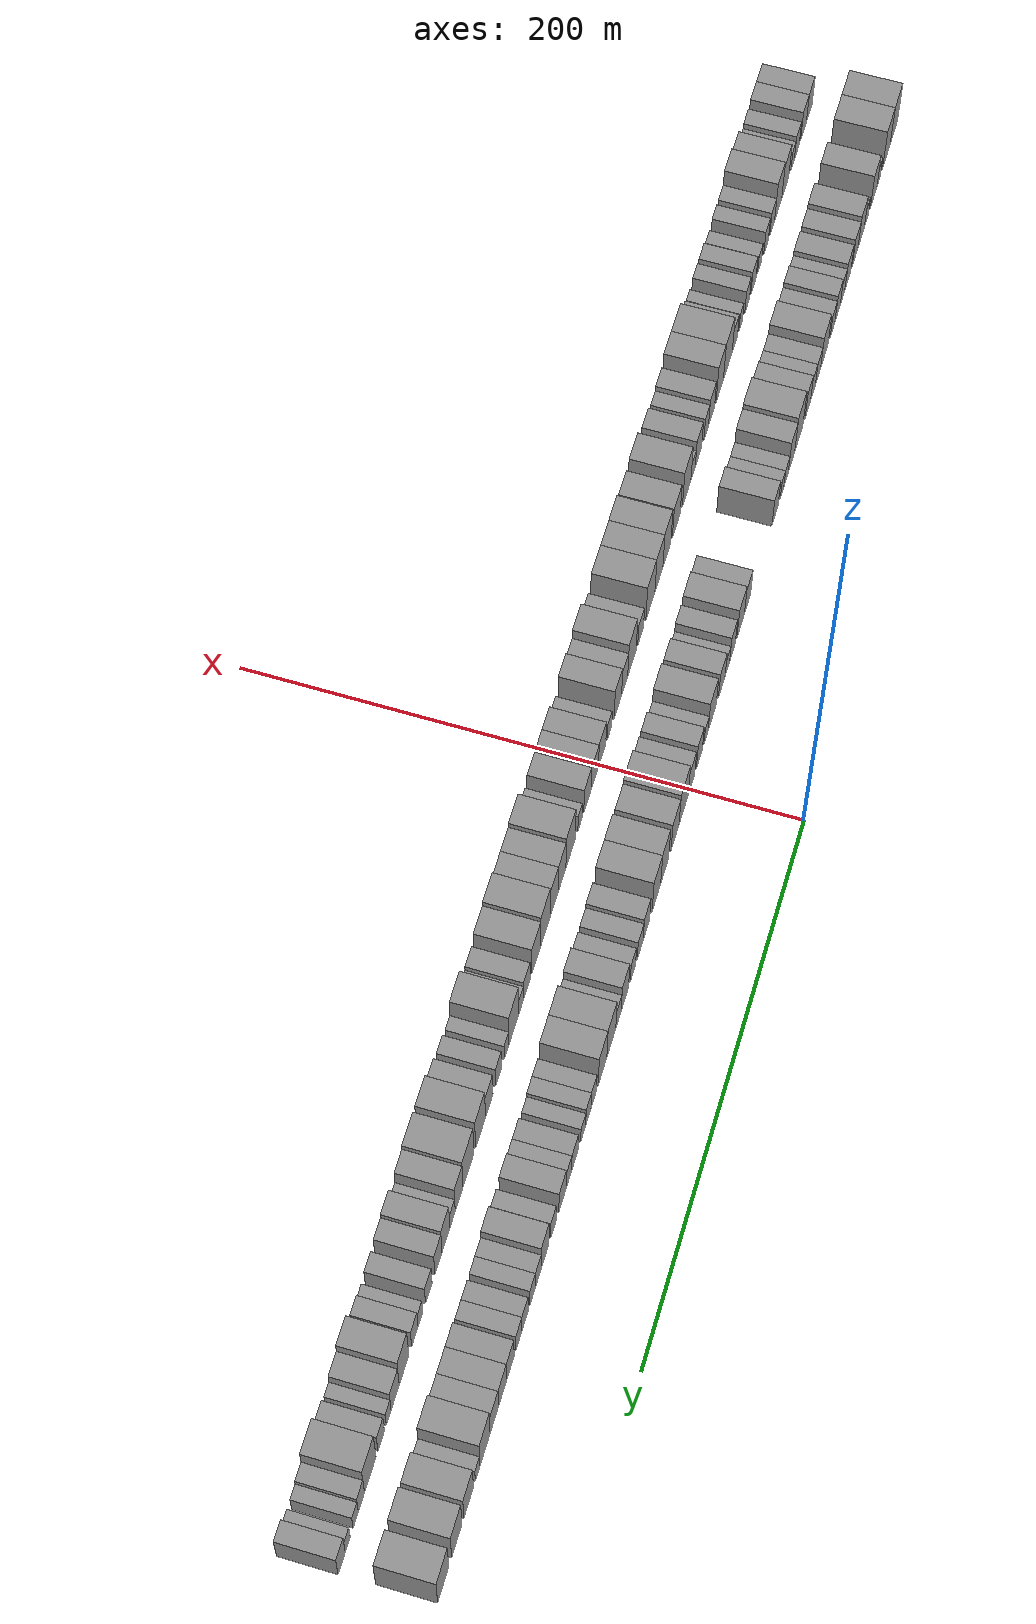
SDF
<sdf version="1.6">
 <world name="default">
  <scene>
   <sky><clouds><speed>12</speed></clouds></sky>
   <ambient>0.4 0.4 0.4 1</ambient>
   <background>0.7 0.7 0.7 1</background>
   <shadows>1</shadows>
  </scene>
  <gravity>0 0 -9.8066</gravity>
  <magnetic_field>6e-06 2.3e-05 -4.2e-05</magnetic_field>
  <physics default="0" name="default_physics" type="ode">
   <ode>
    <solver>
     <type>quick</type>
     <iters>10</iters>
     <sor>1.0</sor>
     <use_dynamic_moi_rescaling>0</use_dynamic_moi_rescaling>
    </solver>
    <constraints>
     <cfm>0</cfm>
     <erp>0.2</erp>
     <contact_max_correcting_vel>100</contact_max_correcting_vel>
     <contact_surface_layer>0.001</contact_surface_layer>
    </constraints>
   </ode>
   <max_step_size>0.004</max_step_size>
   <real_time_factor>1</real_time_factor>
   <real_time_update_rate>250</real_time_update_rate>
  </physics>
  <light name="sun" type="directional">
   <pose>0 0 10 0 0 0</pose>
   <diffuse>0.8 0.8 0.8 1</diffuse>
   <specular>0.2 0.2 0.2 1</specular>
   <attenuation>
    <range>1000</range>
    <constant>0.9</constant>
    <linear>0.01</linear>
    <quadratic>0.001</quadratic>
   </attenuation>
   <direction>-0.5 0.1 -0.9</direction>
  </light>
  <model name="building_1">
   <static>1</static>
   <pose>50.0000 -278.4697 0 0.000000 0.000000 0.000000</pose>
   <link name="link">
    <pose>0 0 12.00 0 0 0</pose>
    <collision name="collision"><geometry><box><size>20.0000 11.0606 24.0000</size></box></geometry></collision>
    <visual name="visual">
     <cast_shadows>0</cast_shadows>
     <geometry><box><size>20.0000 11.0606 24.0000</size></box></geometry>
     <material>
      <script>
       <uri>model://grey_wall/materials/scripts</uri>
       <uri>model://grey_wall/materials/textures</uri>
       <name>vrc/grey_wall</name>
      </script>
     </material>
    </visual>
   </link>
  </model>
  <model name="building_2">
   <static>1</static>
   <pose>50.0000 -267.3348 0 0.000000 0.000000 0.000000</pose>
   <link name="link">
    <pose>0 0 12.00 0 0 0</pose>
    <collision name="collision"><geometry><box><size>20.0000 11.2092 24.0000</size></box></geometry></collision>
    <visual name="visual">
     <cast_shadows>0</cast_shadows>
     <geometry><box><size>20.0000 11.2092 24.0000</size></box></geometry>
     <material>
      <script>
       <uri>model://grey_wall/materials/scripts</uri>
       <uri>model://grey_wall/materials/textures</uri>
       <name>vrc/grey_wall</name>
      </script>
     </material>
    </visual>
   </link>
  </model>
  <model name="building_3">
   <static>1</static>
   <pose>50.0000 -256.1176 0 0.000000 0.000000 0.000000</pose>
   <link name="link">
    <pose>0 0 6.00 0 0 0</pose>
    <collision name="collision"><geometry><box><size>20.0000 5.2254 12.0000</size></box></geometry></collision>
    <visual name="visual">
     <cast_shadows>0</cast_shadows>
     <geometry><box><size>20.0000 5.2254 12.0000</size></box></geometry>
     <material>
      <script>
       <uri>model://grey_wall/materials/scripts</uri>
       <uri>model://grey_wall/materials/textures</uri>
       <name>vrc/grey_wall</name>
      </script>
     </material>
    </visual>
   </link>
  </model>
  <model name="building_4">
   <static>1</static>
   <pose>50.0000 -248.7218 0 0.000000 0.000000 0.000000</pose>
   <link name="link">
    <pose>0 0 10.50 0 0 0</pose>
    <collision name="collision"><geometry><box><size>20.0000 9.5662 21.0000</size></box></geometry></collision>
    <visual name="visual">
     <cast_shadows>0</cast_shadows>
     <geometry><box><size>20.0000 9.5662 21.0000</size></box></geometry>
     <material>
      <script>
       <uri>model://grey_wall/materials/scripts</uri>
       <uri>model://grey_wall/materials/textures</uri>
       <name>vrc/grey_wall</name>
      </script>
     </material>
    </visual>
   </link>
  </model>
  <model name="building_5">
   <static>1</static>
   <pose>50.0000 -238.0001 0 0.000000 0.000000 0.000000</pose>
   <link name="link">
    <pose>0 0 6.00 0 0 0</pose>
    <collision name="collision"><geometry><box><size>20.0000 5.8772 12.0000</size></box></geometry></collision>
    <visual name="visual">
     <cast_shadows>0</cast_shadows>
     <geometry><box><size>20.0000 5.8772 12.0000</size></box></geometry>
     <material>
      <script>
       <uri>model://grey_wall/materials/scripts</uri>
       <uri>model://grey_wall/materials/textures</uri>
       <name>vrc/grey_wall</name>
      </script>
     </material>
    </visual>
   </link>
  </model>
  <model name="building_6">
   <static>1</static>
   <pose>50.0000 -230.4664 0 0.000000 0.000000 0.000000</pose>
   <link name="link">
    <pose>0 0 10.50 0 0 0</pose>
    <collision name="collision"><geometry><box><size>20.0000 9.1902 21.0000</size></box></geometry></collision>
    <visual name="visual">
     <cast_shadows>0</cast_shadows>
     <geometry><box><size>20.0000 9.1902 21.0000</size></box></geometry>
     <material>
      <script>
       <uri>model://grey_wall/materials/scripts</uri>
       <uri>model://grey_wall/materials/textures</uri>
       <name>vrc/grey_wall</name>
      </script>
     </material>
    </visual>
   </link>
  </model>
  <model name="building_7">
   <static>1</static>
   <pose>50.0000 -221.8036 0 0.000000 0.000000 0.000000</pose>
   <link name="link">
    <pose>0 0 9.00 0 0 0</pose>
    <collision name="collision"><geometry><box><size>20.0000 8.1353 18.0000</size></box></geometry></collision>
    <visual name="visual">
     <cast_shadows>0</cast_shadows>
     <geometry><box><size>20.0000 8.1353 18.0000</size></box></geometry>
     <material>
      <script>
       <uri>model://grey_wall/materials/scripts</uri>
       <uri>model://grey_wall/materials/textures</uri>
       <name>vrc/grey_wall</name>
      </script>
     </material>
    </visual>
   </link>
  </model>
  <model name="building_8">
   <static>1</static>
   <pose>50.0000 -211.4116 0 0.000000 0.000000 0.000000</pose>
   <link name="link">
    <pose>0 0 9.00 0 0 0</pose>
    <collision name="collision"><geometry><box><size>20.0000 8.6487 18.0000</size></box></geometry></collision>
    <visual name="visual">
     <cast_shadows>0</cast_shadows>
     <geometry><box><size>20.0000 8.6487 18.0000</size></box></geometry>
     <material>
      <script>
       <uri>model://grey_wall/materials/scripts</uri>
       <uri>model://grey_wall/materials/textures</uri>
       <name>vrc/grey_wall</name>
      </script>
     </material>
    </visual>
   </link>
  </model>
  <model name="building_9">
   <static>1</static>
   <pose>50.0000 -203.8114 0 0.000000 0.000000 0.000000</pose>
   <link name="link">
    <pose>0 0 7.50 0 0 0</pose>
    <collision name="collision"><geometry><box><size>20.0000 6.5516 15.0000</size></box></geometry></collision>
    <visual name="visual">
     <cast_shadows>0</cast_shadows>
     <geometry><box><size>20.0000 6.5516 15.0000</size></box></geometry>
     <material>
      <script>
       <uri>model://grey_wall/materials/scripts</uri>
       <uri>model://grey_wall/materials/textures</uri>
       <name>vrc/grey_wall</name>
      </script>
     </material>
    </visual>
   </link>
  </model>
  <model name="building_10">
   <static>1</static>
   <pose>50.0000 -196.7801 0 0.000000 0.000000 0.000000</pose>
   <link name="link">
    <pose>0 0 9.00 0 0 0</pose>
    <collision name="collision"><geometry><box><size>20.0000 7.5111 18.0000</size></box></geometry></collision>
    <visual name="visual">
     <cast_shadows>0</cast_shadows>
     <geometry><box><size>20.0000 7.5111 18.0000</size></box></geometry>
     <material>
      <script>
       <uri>model://grey_wall/materials/scripts</uri>
       <uri>model://grey_wall/materials/textures</uri>
       <name>vrc/grey_wall</name>
      </script>
     </material>
    </visual>
   </link>
  </model>
  <model name="building_11">
   <static>1</static>
   <pose>50.0000 -189.6941 0 0.000000 0.000000 0.000000</pose>
   <link name="link">
    <pose>0 0 7.50 0 0 0</pose>
    <collision name="collision"><geometry><box><size>20.0000 6.6609 15.0000</size></box></geometry></collision>
    <visual name="visual">
     <cast_shadows>0</cast_shadows>
     <geometry><box><size>20.0000 6.6609 15.0000</size></box></geometry>
     <material>
      <script>
       <uri>model://grey_wall/materials/scripts</uri>
       <uri>model://grey_wall/materials/textures</uri>
       <name>vrc/grey_wall</name>
      </script>
     </material>
    </visual>
   </link>
  </model>
  <model name="building_12">
   <static>1</static>
   <pose>50.0000 -178.1327 0 0.000000 0.000000 0.000000</pose>
   <link name="link">
    <pose>0 0 10.50 0 0 0</pose>
    <collision name="collision"><geometry><box><size>20.0000 10.4620 21.0000</size></box></geometry></collision>
    <visual name="visual">
     <cast_shadows>0</cast_shadows>
     <geometry><box><size>20.0000 10.4620 21.0000</size></box></geometry>
     <material>
      <script>
       <uri>model://grey_wall/materials/scripts</uri>
       <uri>model://grey_wall/materials/textures</uri>
       <name>vrc/grey_wall</name>
      </script>
     </material>
    </visual>
   </link>
  </model>
  <model name="building_13">
   <static>1</static>
   <pose>50.0000 -169.3278 0 0.000000 0.000000 0.000000</pose>
   <link name="link">
    <pose>0 0 7.50 0 0 0</pose>
    <collision name="collision"><geometry><box><size>20.0000 7.1477 15.0000</size></box></geometry></collision>
    <visual name="visual">
     <cast_shadows>0</cast_shadows>
     <geometry><box><size>20.0000 7.1477 15.0000</size></box></geometry>
     <material>
      <script>
       <uri>model://grey_wall/materials/scripts</uri>
       <uri>model://grey_wall/materials/textures</uri>
       <name>vrc/grey_wall</name>
      </script>
     </material>
    </visual>
   </link>
  </model>
  <model name="building_14">
   <static>1</static>
   <pose>50.0000 -162.3910 0 0.000000 0.000000 0.000000</pose>
   <link name="link">
    <pose>0 0 7.50 0 0 0</pose>
    <collision name="collision"><geometry><box><size>20.0000 6.7259 15.0000</size></box></geometry></collision>
    <visual name="visual">
     <cast_shadows>0</cast_shadows>
     <geometry><box><size>20.0000 6.7259 15.0000</size></box></geometry>
     <material>
      <script>
       <uri>model://grey_wall/materials/scripts</uri>
       <uri>model://grey_wall/materials/textures</uri>
       <name>vrc/grey_wall</name>
      </script>
     </material>
    </visual>
   </link>
  </model>
  <model name="building_15">
   <static>1</static>
   <pose>50.0000 -155.2637 0 0.000000 0.000000 0.000000</pose>
   <link name="link">
    <pose>0 0 9.00 0 0 0</pose>
    <collision name="collision"><geometry><box><size>20.0000 7.5286 18.0000</size></box></geometry></collision>
    <visual name="visual">
     <cast_shadows>0</cast_shadows>
     <geometry><box><size>20.0000 7.5286 18.0000</size></box></geometry>
     <material>
      <script>
       <uri>model://grey_wall/materials/scripts</uri>
       <uri>model://grey_wall/materials/textures</uri>
       <name>vrc/grey_wall</name>
      </script>
     </material>
    </visual>
   </link>
  </model>
  <model name="building_16">
   <static>1</static>
   <pose>50.0000 -142.8023 0 0.000000 0.000000 0.000000</pose>
   <link name="link">
    <pose>0 0 12.00 0 0 0</pose>
    <collision name="collision"><geometry><box><size>20.0000 11.3943 24.0000</size></box></geometry></collision>
    <visual name="visual">
     <cast_shadows>0</cast_shadows>
     <geometry><box><size>20.0000 11.3943 24.0000</size></box></geometry>
     <material>
      <script>
       <uri>model://grey_wall/materials/scripts</uri>
       <uri>model://grey_wall/materials/textures</uri>
       <name>vrc/grey_wall</name>
      </script>
     </material>
    </visual>
   </link>
  </model>
  <model name="building_17">
   <static>1</static>
   <pose>50.0000 -132.8097 0 0.000000 0.000000 0.000000</pose>
   <link name="link">
    <pose>0 0 10.50 0 0 0</pose>
    <collision name="collision"><geometry><box><size>20.0000 8.5907 21.0000</size></box></geometry></collision>
    <visual name="visual">
     <cast_shadows>0</cast_shadows>
     <geometry><box><size>20.0000 8.5907 21.0000</size></box></geometry>
     <material>
      <script>
       <uri>model://grey_wall/materials/scripts</uri>
       <uri>model://grey_wall/materials/textures</uri>
       <name>vrc/grey_wall</name>
      </script>
     </material>
    </visual>
   </link>
  </model>
  <model name="building_18">
   <static>1</static>
   <pose>50.0000 -125.5334 0 0.000000 0.000000 0.000000</pose>
   <link name="link">
    <pose>0 0 6.00 0 0 0</pose>
    <collision name="collision"><geometry><box><size>20.0000 5.9619 12.0000</size></box></geometry></collision>
    <visual name="visual">
     <cast_shadows>0</cast_shadows>
     <geometry><box><size>20.0000 5.9619 12.0000</size></box></geometry>
     <material>
      <script>
       <uri>model://grey_wall/materials/scripts</uri>
       <uri>model://grey_wall/materials/textures</uri>
       <name>vrc/grey_wall</name>
      </script>
     </material>
    </visual>
   </link>
  </model>
  <model name="building_19">
   <static>1</static>
   <pose>50.0000 -120.1101 0 0.000000 0.000000 0.000000</pose>
   <link name="link">
    <pose>0 0 6.00 0 0 0</pose>
    <collision name="collision"><geometry><box><size>20.0000 4.8848 12.0000</size></box></geometry></collision>
    <visual name="visual">
     <cast_shadows>0</cast_shadows>
     <geometry><box><size>20.0000 4.8848 12.0000</size></box></geometry>
     <material>
      <script>
       <uri>model://grey_wall/materials/scripts</uri>
       <uri>model://grey_wall/materials/textures</uri>
       <name>vrc/grey_wall</name>
      </script>
     </material>
    </visual>
   </link>
  </model>
  <model name="building_20">
   <static>1</static>
   <pose>50.0000 -110.5472 0 0.000000 0.000000 0.000000</pose>
   <link name="link">
    <pose>0 0 9.00 0 0 0</pose>
    <collision name="collision"><geometry><box><size>20.0000 8.2411 18.0000</size></box></geometry></collision>
    <visual name="visual">
     <cast_shadows>0</cast_shadows>
     <geometry><box><size>20.0000 8.2411 18.0000</size></box></geometry>
     <material>
      <script>
       <uri>model://grey_wall/materials/scripts</uri>
       <uri>model://grey_wall/materials/textures</uri>
       <name>vrc/grey_wall</name>
      </script>
     </material>
    </visual>
   </link>
  </model>
  <model name="building_21">
   <static>1</static>
   <pose>50.0000 -73.9878 0 0.000000 0.000000 0.000000</pose>
   <link name="link">
    <pose>0 0 9.00 0 0 0</pose>
    <collision name="collision"><geometry><box><size>20.0000 8.2926 18.0000</size></box></geometry></collision>
    <visual name="visual">
     <cast_shadows>0</cast_shadows>
     <geometry><box><size>20.0000 8.2926 18.0000</size></box></geometry>
     <material>
      <script>
       <uri>model://grey_wall/materials/scripts</uri>
       <uri>model://grey_wall/materials/textures</uri>
       <name>vrc/grey_wall</name>
      </script>
     </material>
    </visual>
   </link>
  </model>
  <model name="building_22">
   <static>1</static>
   <pose>50.0000 -64.9480 0 0.000000 0.000000 0.000000</pose>
   <link name="link">
    <pose>0 0 10.50 0 0 0</pose>
    <collision name="collision"><geometry><box><size>20.0000 9.7870 21.0000</size></box></geometry></collision>
    <visual name="visual">
     <cast_shadows>0</cast_shadows>
     <geometry><box><size>20.0000 9.7870 21.0000</size></box></geometry>
     <material>
      <script>
       <uri>model://grey_wall/materials/scripts</uri>
       <uri>model://grey_wall/materials/textures</uri>
       <name>vrc/grey_wall</name>
      </script>
     </material>
    </visual>
   </link>
  </model>
  <model name="building_23">
   <static>1</static>
   <pose>50.0000 -54.3780 0 0.000000 0.000000 0.000000</pose>
   <link name="link">
    <pose>0 0 9.00 0 0 0</pose>
    <collision name="collision"><geometry><box><size>20.0000 7.3532 18.0000</size></box></geometry></collision>
    <visual name="visual">
     <cast_shadows>0</cast_shadows>
     <geometry><box><size>20.0000 7.3532 18.0000</size></box></geometry>
     <material>
      <script>
       <uri>model://grey_wall/materials/scripts</uri>
       <uri>model://grey_wall/materials/textures</uri>
       <name>vrc/grey_wall</name>
      </script>
     </material>
    </visual>
   </link>
  </model>
  <model name="building_24">
   <static>1</static>
   <pose>50.0000 -47.7225 0 0.000000 0.000000 0.000000</pose>
   <link name="link">
    <pose>0 0 6.00 0 0 0</pose>
    <collision name="collision"><geometry><box><size>20.0000 5.9577 12.0000</size></box></geometry></collision>
    <visual name="visual">
     <cast_shadows>0</cast_shadows>
     <geometry><box><size>20.0000 5.9577 12.0000</size></box></geometry>
     <material>
      <script>
       <uri>model://grey_wall/materials/scripts</uri>
       <uri>model://grey_wall/materials/textures</uri>
       <name>vrc/grey_wall</name>
      </script>
     </material>
    </visual>
   </link>
  </model>
  <model name="building_25">
   <static>1</static>
   <pose>50.0000 -40.4584 0 0.000000 0.000000 0.000000</pose>
   <link name="link">
    <pose>0 0 9.00 0 0 0</pose>
    <collision name="collision"><geometry><box><size>20.0000 8.5706 18.0000</size></box></geometry></collision>
    <visual name="visual">
     <cast_shadows>0</cast_shadows>
     <geometry><box><size>20.0000 8.5706 18.0000</size></box></geometry>
     <material>
      <script>
       <uri>model://grey_wall/materials/scripts</uri>
       <uri>model://grey_wall/materials/textures</uri>
       <name>vrc/grey_wall</name>
      </script>
     </material>
    </visual>
   </link>
  </model>
  <model name="building_26">
   <static>1</static>
   <pose>50.0000 -28.0884 0 0.000000 0.000000 0.000000</pose>
   <link name="link">
    <pose>0 0 10.50 0 0 0</pose>
    <collision name="collision"><geometry><box><size>20.0000 10.1693 21.0000</size></box></geometry></collision>
    <visual name="visual">
     <cast_shadows>0</cast_shadows>
     <geometry><box><size>20.0000 10.1693 21.0000</size></box></geometry>
     <material>
      <script>
       <uri>model://grey_wall/materials/scripts</uri>
       <uri>model://grey_wall/materials/textures</uri>
       <name>vrc/grey_wall</name>
      </script>
     </material>
    </visual>
   </link>
  </model>
  <model name="building_27">
   <static>1</static>
   <pose>50.0000 -20.3685 0 0.000000 0.000000 0.000000</pose>
   <link name="link">
    <pose>0 0 6.00 0 0 0</pose>
    <collision name="collision"><geometry><box><size>20.0000 5.2705 12.0000</size></box></geometry></collision>
    <visual name="visual">
     <cast_shadows>0</cast_shadows>
     <geometry><box><size>20.0000 5.2705 12.0000</size></box></geometry>
     <material>
      <script>
       <uri>model://grey_wall/materials/scripts</uri>
       <uri>model://grey_wall/materials/textures</uri>
       <name>vrc/grey_wall</name>
      </script>
     </material>
    </visual>
   </link>
  </model>
  <model name="building_28">
   <static>1</static>
   <pose>50.0000 -11.8762 0 0.000000 0.000000 0.000000</pose>
   <link name="link">
    <pose>0 0 9.00 0 0 0</pose>
    <collision name="collision"><geometry><box><size>20.0000 7.7143 18.0000</size></box></geometry></collision>
    <visual name="visual">
     <cast_shadows>0</cast_shadows>
     <geometry><box><size>20.0000 7.7143 18.0000</size></box></geometry>
     <material>
      <script>
       <uri>model://grey_wall/materials/scripts</uri>
       <uri>model://grey_wall/materials/textures</uri>
       <name>vrc/grey_wall</name>
      </script>
     </material>
    </visual>
   </link>
  </model>
  <model name="building_29">
   <static>1</static>
   <pose>50.0000 -1.8797 0 0.000000 0.000000 0.000000</pose>
   <link name="link">
    <pose>0 0 9.00 0 0 0</pose>
    <collision name="collision"><geometry><box><size>20.0000 8.2786 18.0000</size></box></geometry></collision>
    <visual name="visual">
     <cast_shadows>0</cast_shadows>
     <geometry><box><size>20.0000 8.2786 18.0000</size></box></geometry>
     <material>
      <script>
       <uri>model://grey_wall/materials/scripts</uri>
       <uri>model://grey_wall/materials/textures</uri>
       <name>vrc/grey_wall</name>
      </script>
     </material>
    </visual>
   </link>
  </model>
  <model name="building_30">
   <static>1</static>
   <pose>50.0000 7.9761 0 0.000000 0.000000 0.000000</pose>
   <link name="link">
    <pose>0 0 12.00 0 0 0</pose>
    <collision name="collision"><geometry><box><size>20.0000 11.4330 24.0000</size></box></geometry></collision>
    <visual name="visual">
     <cast_shadows>0</cast_shadows>
     <geometry><box><size>20.0000 11.4330 24.0000</size></box></geometry>
     <material>
      <script>
       <uri>model://grey_wall/materials/scripts</uri>
       <uri>model://grey_wall/materials/textures</uri>
       <name>vrc/grey_wall</name>
      </script>
     </material>
    </visual>
   </link>
  </model>
  <model name="building_31">
   <static>1</static>
   <pose>50.0000 18.6461 0 0.000000 0.000000 0.000000</pose>
   <link name="link">
    <pose>0 0 10.50 0 0 0</pose>
    <collision name="collision"><geometry><box><size>20.0000 9.9068 21.0000</size></box></geometry></collision>
    <visual name="visual">
     <cast_shadows>0</cast_shadows>
     <geometry><box><size>20.0000 9.9068 21.0000</size></box></geometry>
     <material>
      <script>
       <uri>model://grey_wall/materials/scripts</uri>
       <uri>model://grey_wall/materials/textures</uri>
       <name>vrc/grey_wall</name>
      </script>
     </material>
    </visual>
   </link>
  </model>
  <model name="building_32">
   <static>1</static>
   <pose>50.0000 31.4543 0 0.000000 0.000000 0.000000</pose>
   <link name="link">
    <pose>0 0 12.00 0 0 0</pose>
    <collision name="collision"><geometry><box><size>20.0000 9.7096 24.0000</size></box></geometry></collision>
    <visual name="visual">
     <cast_shadows>0</cast_shadows>
     <geometry><box><size>20.0000 9.7096 24.0000</size></box></geometry>
     <material>
      <script>
       <uri>model://grey_wall/materials/scripts</uri>
       <uri>model://grey_wall/materials/textures</uri>
       <name>vrc/grey_wall</name>
      </script>
     </material>
    </visual>
   </link>
  </model>
  <model name="building_33">
   <static>1</static>
   <pose>50.0000 41.5467 0 0.000000 0.000000 0.000000</pose>
   <link name="link">
    <pose>0 0 12.00 0 0 0</pose>
    <collision name="collision"><geometry><box><size>20.0000 10.4753 24.0000</size></box></geometry></collision>
    <visual name="visual">
     <cast_shadows>0</cast_shadows>
     <geometry><box><size>20.0000 10.4753 24.0000</size></box></geometry>
     <material>
      <script>
       <uri>model://grey_wall/materials/scripts</uri>
       <uri>model://grey_wall/materials/textures</uri>
       <name>vrc/grey_wall</name>
      </script>
     </material>
    </visual>
   </link>
  </model>
  <model name="building_34">
   <static>1</static>
   <pose>50.0000 53.7701 0 0.000000 0.000000 0.000000</pose>
   <link name="link">
    <pose>0 0 9.00 0 0 0</pose>
    <collision name="collision"><geometry><box><size>20.0000 7.9716 18.0000</size></box></geometry></collision>
    <visual name="visual">
     <cast_shadows>0</cast_shadows>
     <geometry><box><size>20.0000 7.9716 18.0000</size></box></geometry>
     <material>
      <script>
       <uri>model://grey_wall/materials/scripts</uri>
       <uri>model://grey_wall/materials/textures</uri>
       <name>vrc/grey_wall</name>
      </script>
     </material>
    </visual>
   </link>
  </model>
  <model name="building_35">
   <static>1</static>
   <pose>50.0000 61.3067 0 0.000000 0.000000 0.000000</pose>
   <link name="link">
    <pose>0 0 7.50 0 0 0</pose>
    <collision name="collision"><geometry><box><size>20.0000 7.1015 15.0000</size></box></geometry></collision>
    <visual name="visual">
     <cast_shadows>0</cast_shadows>
     <geometry><box><size>20.0000 7.1015 15.0000</size></box></geometry>
     <material>
      <script>
       <uri>model://grey_wall/materials/scripts</uri>
       <uri>model://grey_wall/materials/textures</uri>
       <name>vrc/grey_wall</name>
      </script>
     </material>
    </visual>
   </link>
  </model>
  <model name="building_36">
   <static>1</static>
   <pose>50.0000 70.0731 0 0.000000 0.000000 0.000000</pose>
   <link name="link">
    <pose>0 0 7.50 0 0 0</pose>
    <collision name="collision"><geometry><box><size>20.0000 6.4313 15.0000</size></box></geometry></collision>
    <visual name="visual">
     <cast_shadows>0</cast_shadows>
     <geometry><box><size>20.0000 6.4313 15.0000</size></box></geometry>
     <material>
      <script>
       <uri>model://grey_wall/materials/scripts</uri>
       <uri>model://grey_wall/materials/textures</uri>
       <name>vrc/grey_wall</name>
      </script>
     </material>
    </visual>
   </link>
  </model>
  <model name="building_37">
   <static>1</static>
   <pose>50.0000 79.7075 0 0.000000 0.000000 0.000000</pose>
   <link name="link">
    <pose>0 0 10.50 0 0 0</pose>
    <collision name="collision"><geometry><box><size>20.0000 8.8375 21.0000</size></box></geometry></collision>
    <visual name="visual">
     <cast_shadows>0</cast_shadows>
     <geometry><box><size>20.0000 8.8375 21.0000</size></box></geometry>
     <material>
      <script>
       <uri>model://grey_wall/materials/scripts</uri>
       <uri>model://grey_wall/materials/textures</uri>
       <name>vrc/grey_wall</name>
      </script>
     </material>
    </visual>
   </link>
  </model>
  <model name="building_38">
   <static>1</static>
   <pose>50.0000 87.2910 0 0.000000 0.000000 0.000000</pose>
   <link name="link">
    <pose>0 0 7.50 0 0 0</pose>
    <collision name="collision"><geometry><box><size>20.0000 6.3293 15.0000</size></box></geometry></collision>
    <visual name="visual">
     <cast_shadows>0</cast_shadows>
     <geometry><box><size>20.0000 6.3293 15.0000</size></box></geometry>
     <material>
      <script>
       <uri>model://grey_wall/materials/scripts</uri>
       <uri>model://grey_wall/materials/textures</uri>
       <name>vrc/grey_wall</name>
      </script>
     </material>
    </visual>
   </link>
  </model>
  <model name="building_39">
   <static>1</static>
   <pose>50.0000 95.7228 0 0.000000 0.000000 0.000000</pose>
   <link name="link">
    <pose>0 0 12.00 0 0 0</pose>
    <collision name="collision"><geometry><box><size>20.0000 10.5344 24.0000</size></box></geometry></collision>
    <visual name="visual">
     <cast_shadows>0</cast_shadows>
     <geometry><box><size>20.0000 10.5344 24.0000</size></box></geometry>
     <material>
      <script>
       <uri>model://grey_wall/materials/scripts</uri>
       <uri>model://grey_wall/materials/textures</uri>
       <name>vrc/grey_wall</name>
      </script>
     </material>
    </visual>
   </link>
  </model>
  <model name="building_40">
   <static>1</static>
   <pose>50.0000 106.0783 0 0.000000 0.000000 0.000000</pose>
   <link name="link">
    <pose>0 0 12.00 0 0 0</pose>
    <collision name="collision"><geometry><box><size>20.0000 10.1767 24.0000</size></box></geometry></collision>
    <visual name="visual">
     <cast_shadows>0</cast_shadows>
     <geometry><box><size>20.0000 10.1767 24.0000</size></box></geometry>
     <material>
      <script>
       <uri>model://grey_wall/materials/scripts</uri>
       <uri>model://grey_wall/materials/textures</uri>
       <name>vrc/grey_wall</name>
      </script>
     </material>
    </visual>
   </link>
  </model>
  <model name="building_41">
   <static>1</static>
   <pose>50.0000 116.3353 0 0.000000 0.000000 0.000000</pose>
   <link name="link">
    <pose>0 0 7.50 0 0 0</pose>
    <collision name="collision"><geometry><box><size>20.0000 6.3371 15.0000</size></box></geometry></collision>
    <visual name="visual">
     <cast_shadows>0</cast_shadows>
     <geometry><box><size>20.0000 6.3371 15.0000</size></box></geometry>
     <material>
      <script>
       <uri>model://grey_wall/materials/scripts</uri>
       <uri>model://grey_wall/materials/textures</uri>
       <name>vrc/grey_wall</name>
      </script>
     </material>
    </visual>
   </link>
  </model>
  <model name="building_42">
   <static>1</static>
   <pose>50.0000 122.5918 0 0.000000 0.000000 0.000000</pose>
   <link name="link">
    <pose>0 0 7.50 0 0 0</pose>
    <collision name="collision"><geometry><box><size>20.0000 6.1759 15.0000</size></box></geometry></collision>
    <visual name="visual">
     <cast_shadows>0</cast_shadows>
     <geometry><box><size>20.0000 6.1759 15.0000</size></box></geometry>
     <material>
      <script>
       <uri>model://grey_wall/materials/scripts</uri>
       <uri>model://grey_wall/materials/textures</uri>
       <name>vrc/grey_wall</name>
      </script>
     </material>
    </visual>
   </link>
  </model>
  <model name="building_43">
   <static>1</static>
   <pose>50.0000 128.5750 0 0.000000 0.000000 0.000000</pose>
   <link name="link">
    <pose>0 0 6.00 0 0 0</pose>
    <collision name="collision"><geometry><box><size>20.0000 5.7906 12.0000</size></box></geometry></collision>
    <visual name="visual">
     <cast_shadows>0</cast_shadows>
     <geometry><box><size>20.0000 5.7906 12.0000</size></box></geometry>
     <material>
      <script>
       <uri>model://grey_wall/materials/scripts</uri>
       <uri>model://grey_wall/materials/textures</uri>
       <name>vrc/grey_wall</name>
      </script>
     </material>
    </visual>
   </link>
  </model>
  <model name="building_44">
   <static>1</static>
   <pose>50.0000 138.1663 0 0.000000 0.000000 0.000000</pose>
   <link name="link">
    <pose>0 0 7.50 0 0 0</pose>
    <collision name="collision"><geometry><box><size>20.0000 7.3919 15.0000</size></box></geometry></collision>
    <visual name="visual">
     <cast_shadows>0</cast_shadows>
     <geometry><box><size>20.0000 7.3919 15.0000</size></box></geometry>
     <material>
      <script>
       <uri>model://grey_wall/materials/scripts</uri>
       <uri>model://grey_wall/materials/textures</uri>
       <name>vrc/grey_wall</name>
      </script>
     </material>
    </visual>
   </link>
  </model>
  <model name="building_45">
   <static>1</static>
   <pose>50.0000 144.9747 0 0.000000 0.000000 0.000000</pose>
   <link name="link">
    <pose>0 0 7.50 0 0 0</pose>
    <collision name="collision"><geometry><box><size>20.0000 6.2251 15.0000</size></box></geometry></collision>
    <visual name="visual">
     <cast_shadows>0</cast_shadows>
     <geometry><box><size>20.0000 6.2251 15.0000</size></box></geometry>
     <material>
      <script>
       <uri>model://grey_wall/materials/scripts</uri>
       <uri>model://grey_wall/materials/textures</uri>
       <name>vrc/grey_wall</name>
      </script>
     </material>
    </visual>
   </link>
  </model>
  <model name="building_46">
   <static>1</static>
   <pose>50.0000 152.2790 0 0.000000 0.000000 0.000000</pose>
   <link name="link">
    <pose>0 0 9.00 0 0 0</pose>
    <collision name="collision"><geometry><box><size>20.0000 8.3834 18.0000</size></box></geometry></collision>
    <visual name="visual">
     <cast_shadows>0</cast_shadows>
     <geometry><box><size>20.0000 8.3834 18.0000</size></box></geometry>
     <material>
      <script>
       <uri>model://grey_wall/materials/scripts</uri>
       <uri>model://grey_wall/materials/textures</uri>
       <name>vrc/grey_wall</name>
      </script>
     </material>
    </visual>
   </link>
  </model>
  <model name="building_47">
   <static>1</static>
   <pose>50.0000 162.5664 0 0.000000 0.000000 0.000000</pose>
   <link name="link">
    <pose>0 0 7.50 0 0 0</pose>
    <collision name="collision"><geometry><box><size>20.0000 6.1914 15.0000</size></box></geometry></collision>
    <visual name="visual">
     <cast_shadows>0</cast_shadows>
     <geometry><box><size>20.0000 6.1914 15.0000</size></box></geometry>
     <material>
      <script>
       <uri>model://grey_wall/materials/scripts</uri>
       <uri>model://grey_wall/materials/textures</uri>
       <name>vrc/grey_wall</name>
      </script>
     </material>
    </visual>
   </link>
  </model>
  <model name="building_48">
   <static>1</static>
   <pose>50.0000 172.0053 0 0.000000 0.000000 0.000000</pose>
   <link name="link">
    <pose>0 0 10.50 0 0 0</pose>
    <collision name="collision"><geometry><box><size>20.0000 8.6865 21.0000</size></box></geometry></collision>
    <visual name="visual">
     <cast_shadows>0</cast_shadows>
     <geometry><box><size>20.0000 8.6865 21.0000</size></box></geometry>
     <material>
      <script>
       <uri>model://grey_wall/materials/scripts</uri>
       <uri>model://grey_wall/materials/textures</uri>
       <name>vrc/grey_wall</name>
      </script>
     </material>
    </visual>
   </link>
  </model>
  <model name="building_49">
   <static>1</static>
   <pose>50.0000 179.5448 0 0.000000 0.000000 0.000000</pose>
   <link name="link">
    <pose>0 0 7.50 0 0 0</pose>
    <collision name="collision"><geometry><box><size>20.0000 6.3926 15.0000</size></box></geometry></collision>
    <visual name="visual">
     <cast_shadows>0</cast_shadows>
     <geometry><box><size>20.0000 6.3926 15.0000</size></box></geometry>
     <material>
      <script>
       <uri>model://grey_wall/materials/scripts</uri>
       <uri>model://grey_wall/materials/textures</uri>
       <name>vrc/grey_wall</name>
      </script>
     </material>
    </visual>
   </link>
  </model>
  <model name="building_50">
   <static>1</static>
   <pose>50.0000 185.8304 0 0.000000 0.000000 0.000000</pose>
   <link name="link">
    <pose>0 0 7.50 0 0 0</pose>
    <collision name="collision"><geometry><box><size>20.0000 6.1786 15.0000</size></box></geometry></collision>
    <visual name="visual">
     <cast_shadows>0</cast_shadows>
     <geometry><box><size>20.0000 6.1786 15.0000</size></box></geometry>
     <material>
      <script>
       <uri>model://grey_wall/materials/scripts</uri>
       <uri>model://grey_wall/materials/textures</uri>
       <name>vrc/grey_wall</name>
      </script>
     </material>
    </visual>
   </link>
  </model>
  <model name="building_51">
   <static>1</static>
   <pose>50.0000 194.2965 0 0.000000 0.000000 0.000000</pose>
   <link name="link">
    <pose>0 0 7.50 0 0 0</pose>
    <collision name="collision"><geometry><box><size>20.0000 6.7537 15.0000</size></box></geometry></collision>
    <visual name="visual">
     <cast_shadows>0</cast_shadows>
     <geometry><box><size>20.0000 6.7537 15.0000</size></box></geometry>
     <material>
      <script>
       <uri>model://grey_wall/materials/scripts</uri>
       <uri>model://grey_wall/materials/textures</uri>
       <name>vrc/grey_wall</name>
      </script>
     </material>
    </visual>
   </link>
  </model>
  <model name="building_52">
   <static>1</static>
   <pose>50.0000 201.0290 0 0.000000 0.000000 0.000000</pose>
   <link name="link">
    <pose>0 0 7.50 0 0 0</pose>
    <collision name="collision"><geometry><box><size>20.0000 6.7113 15.0000</size></box></geometry></collision>
    <visual name="visual">
     <cast_shadows>0</cast_shadows>
     <geometry><box><size>20.0000 6.7113 15.0000</size></box></geometry>
     <material>
      <script>
       <uri>model://grey_wall/materials/scripts</uri>
       <uri>model://grey_wall/materials/textures</uri>
       <name>vrc/grey_wall</name>
      </script>
     </material>
    </visual>
   </link>
  </model>
  <model name="building_53">
   <static>1</static>
   <pose>50.0000 210.4382 0 0.000000 0.000000 0.000000</pose>
   <link name="link">
    <pose>0 0 9.00 0 0 0</pose>
    <collision name="collision"><geometry><box><size>20.0000 8.1071 18.0000</size></box></geometry></collision>
    <visual name="visual">
     <cast_shadows>0</cast_shadows>
     <geometry><box><size>20.0000 8.1071 18.0000</size></box></geometry>
     <material>
      <script>
       <uri>model://grey_wall/materials/scripts</uri>
       <uri>model://grey_wall/materials/textures</uri>
       <name>vrc/grey_wall</name>
      </script>
     </material>
    </visual>
   </link>
  </model>
  <model name="building_54">
   <static>1</static>
   <pose>50.0000 218.9860 0 0.000000 0.000000 0.000000</pose>
   <link name="link">
    <pose>0 0 9.00 0 0 0</pose>
    <collision name="collision"><geometry><box><size>20.0000 8.9886 18.0000</size></box></geometry></collision>
    <visual name="visual">
     <cast_shadows>0</cast_shadows>
     <geometry><box><size>20.0000 8.9886 18.0000</size></box></geometry>
     <material>
      <script>
       <uri>model://grey_wall/materials/scripts</uri>
       <uri>model://grey_wall/materials/textures</uri>
       <name>vrc/grey_wall</name>
      </script>
     </material>
    </visual>
   </link>
  </model>
  <model name="building_55">
   <static>1</static>
   <pose>50.0000 227.9775 0 0.000000 0.000000 0.000000</pose>
   <link name="link">
    <pose>0 0 9.00 0 0 0</pose>
    <collision name="collision"><geometry><box><size>20.0000 8.9945 18.0000</size></box></geometry></collision>
    <visual name="visual">
     <cast_shadows>0</cast_shadows>
     <geometry><box><size>20.0000 8.9945 18.0000</size></box></geometry>
     <material>
      <script>
       <uri>model://grey_wall/materials/scripts</uri>
       <uri>model://grey_wall/materials/textures</uri>
       <name>vrc/grey_wall</name>
      </script>
     </material>
    </visual>
   </link>
  </model>
  <model name="building_56">
   <static>1</static>
   <pose>50.0000 237.9417 0 0.000000 0.000000 0.000000</pose>
   <link name="link">
    <pose>0 0 12.00 0 0 0</pose>
    <collision name="collision"><geometry><box><size>20.0000 10.9339 24.0000</size></box></geometry></collision>
    <visual name="visual">
     <cast_shadows>0</cast_shadows>
     <geometry><box><size>20.0000 10.9339 24.0000</size></box></geometry>
     <material>
      <script>
       <uri>model://grey_wall/materials/scripts</uri>
       <uri>model://grey_wall/materials/textures</uri>
       <name>vrc/grey_wall</name>
      </script>
     </material>
    </visual>
   </link>
  </model>
  <model name="building_57">
   <static>1</static>
   <pose>50.0000 245.8787 0 0.000000 0.000000 0.000000</pose>
   <link name="link">
    <pose>0 0 6.00 0 0 0</pose>
    <collision name="collision"><geometry><box><size>20.0000 4.9400 12.0000</size></box></geometry></collision>
    <visual name="visual">
     <cast_shadows>0</cast_shadows>
     <geometry><box><size>20.0000 4.9400 12.0000</size></box></geometry>
     <material>
      <script>
       <uri>model://grey_wall/materials/scripts</uri>
       <uri>model://grey_wall/materials/textures</uri>
       <name>vrc/grey_wall</name>
      </script>
     </material>
    </visual>
   </link>
  </model>
  <model name="building_58">
   <static>1</static>
   <pose>50.0000 255.4350 0 0.000000 0.000000 0.000000</pose>
   <link name="link">
    <pose>0 0 10.50 0 0 0</pose>
    <collision name="collision"><geometry><box><size>20.0000 10.1725 21.0000</size></box></geometry></collision>
    <visual name="visual">
     <cast_shadows>0</cast_shadows>
     <geometry><box><size>20.0000 10.1725 21.0000</size></box></geometry>
     <material>
      <script>
       <uri>model://grey_wall/materials/scripts</uri>
       <uri>model://grey_wall/materials/textures</uri>
       <name>vrc/grey_wall</name>
      </script>
     </material>
    </visual>
   </link>
  </model>
  <model name="building_59">
   <static>1</static>
   <pose>50.0000 267.9128 0 0.000000 0.000000 0.000000</pose>
   <link name="link">
    <pose>0 0 12.00 0 0 0</pose>
    <collision name="collision"><geometry><box><size>20.0000 10.7831 24.0000</size></box></geometry></collision>
    <visual name="visual">
     <cast_shadows>0</cast_shadows>
     <geometry><box><size>20.0000 10.7831 24.0000</size></box></geometry>
     <material>
      <script>
       <uri>model://grey_wall/materials/scripts</uri>
       <uri>model://grey_wall/materials/textures</uri>
       <name>vrc/grey_wall</name>
      </script>
     </material>
    </visual>
   </link>
  </model>
  <model name="building_60">
   <static>1</static>
   <pose>50.0000 282.1085 0 0.000000 0.000000 0.000000</pose>
   <link name="link">
    <pose>0 0 12.00 0 0 0</pose>
    <collision name="collision"><geometry><box><size>20.0000 11.6082 24.0000</size></box></geometry></collision>
    <visual name="visual">
     <cast_shadows>0</cast_shadows>
     <geometry><box><size>20.0000 11.6082 24.0000</size></box></geometry>
     <material>
      <script>
       <uri>model://grey_wall/materials/scripts</uri>
       <uri>model://grey_wall/materials/textures</uri>
       <name>vrc/grey_wall</name>
      </script>
     </material>
    </visual>
   </link>
  </model>
  <model name="building_61">
   <static>1</static>
   <pose>82.0000 -277.8554 0 0.000000 0.000000 0.000000</pose>
   <link name="link">
    <pose>0 0 9.00 0 0 0</pose>
    <collision name="collision"><geometry><box><size>20.0000 8.2891 18.0000</size></box></geometry></collision>
    <visual name="visual">
     <cast_shadows>0</cast_shadows>
     <geometry><box><size>20.0000 8.2891 18.0000</size></box></geometry>
     <material>
      <script>
       <uri>model://grey_wall/materials/scripts</uri>
       <uri>model://grey_wall/materials/textures</uri>
       <name>vrc/grey_wall</name>
      </script>
     </material>
    </visual>
   </link>
  </model>
  <model name="building_62">
   <static>1</static>
   <pose>82.0000 -269.5396 0 0.000000 0.000000 0.000000</pose>
   <link name="link">
    <pose>0 0 9.00 0 0 0</pose>
    <collision name="collision"><geometry><box><size>20.0000 8.3425 18.0000</size></box></geometry></collision>
    <visual name="visual">
     <cast_shadows>0</cast_shadows>
     <geometry><box><size>20.0000 8.3425 18.0000</size></box></geometry>
     <material>
      <script>
       <uri>model://grey_wall/materials/scripts</uri>
       <uri>model://grey_wall/materials/textures</uri>
       <name>vrc/grey_wall</name>
      </script>
     </material>
    </visual>
   </link>
  </model>
  <model name="building_63">
   <static>1</static>
   <pose>82.0000 -259.9513 0 0.000000 0.000000 0.000000</pose>
   <link name="link">
    <pose>0 0 7.50 0 0 0</pose>
    <collision name="collision"><geometry><box><size>20.0000 6.8341 15.0000</size></box></geometry></collision>
    <visual name="visual">
     <cast_shadows>0</cast_shadows>
     <geometry><box><size>20.0000 6.8341 15.0000</size></box></geometry>
     <material>
      <script>
       <uri>model://grey_wall/materials/scripts</uri>
       <uri>model://grey_wall/materials/textures</uri>
       <name>vrc/grey_wall</name>
      </script>
     </material>
    </visual>
   </link>
  </model>
  <model name="building_64">
   <static>1</static>
   <pose>82.0000 -254.0857 0 0.000000 0.000000 0.000000</pose>
   <link name="link">
    <pose>0 0 6.00 0 0 0</pose>
    <collision name="collision"><geometry><box><size>20.0000 4.8971 12.0000</size></box></geometry></collision>
    <visual name="visual">
     <cast_shadows>0</cast_shadows>
     <geometry><box><size>20.0000 4.8971 12.0000</size></box></geometry>
     <material>
      <script>
       <uri>model://grey_wall/materials/scripts</uri>
       <uri>model://grey_wall/materials/textures</uri>
       <name>vrc/grey_wall</name>
      </script>
     </material>
    </visual>
   </link>
  </model>
  <model name="building_65">
   <static>1</static>
   <pose>82.0000 -243.6845 0 0.000000 0.000000 0.000000</pose>
   <link name="link">
    <pose>0 0 10.50 0 0 0</pose>
    <collision name="collision"><geometry><box><size>20.0000 9.9052 21.0000</size></box></geometry></collision>
    <visual name="visual">
     <cast_shadows>0</cast_shadows>
     <geometry><box><size>20.0000 9.9052 21.0000</size></box></geometry>
     <material>
      <script>
       <uri>model://grey_wall/materials/scripts</uri>
       <uri>model://grey_wall/materials/textures</uri>
       <name>vrc/grey_wall</name>
      </script>
     </material>
    </visual>
   </link>
  </model>
  <model name="building_66">
   <static>1</static>
   <pose>82.0000 -233.7292 0 0.000000 0.000000 0.000000</pose>
   <link name="link">
    <pose>0 0 12.00 0 0 0</pose>
    <collision name="collision"><geometry><box><size>20.0000 10.0055 24.0000</size></box></geometry></collision>
    <visual name="visual">
     <cast_shadows>0</cast_shadows>
     <geometry><box><size>20.0000 10.0055 24.0000</size></box></geometry>
     <material>
      <script>
       <uri>model://grey_wall/materials/scripts</uri>
       <uri>model://grey_wall/materials/textures</uri>
       <name>vrc/grey_wall</name>
      </script>
     </material>
    </visual>
   </link>
  </model>
  <model name="building_67">
   <static>1</static>
   <pose>82.0000 -225.3629 0 0.000000 0.000000 0.000000</pose>
   <link name="link">
    <pose>0 0 7.50 0 0 0</pose>
    <collision name="collision"><geometry><box><size>20.0000 6.7270 15.0000</size></box></geometry></collision>
    <visual name="visual">
     <cast_shadows>0</cast_shadows>
     <geometry><box><size>20.0000 6.7270 15.0000</size></box></geometry>
     <material>
      <script>
       <uri>model://grey_wall/materials/scripts</uri>
       <uri>model://grey_wall/materials/textures</uri>
       <name>vrc/grey_wall</name>
      </script>
     </material>
    </visual>
   </link>
  </model>
  <model name="building_68">
   <static>1</static>
   <pose>82.0000 -216.8171 0 0.000000 0.000000 0.000000</pose>
   <link name="link">
    <pose>0 0 7.50 0 0 0</pose>
    <collision name="collision"><geometry><box><size>20.0000 6.3647 15.0000</size></box></geometry></collision>
    <visual name="visual">
     <cast_shadows>0</cast_shadows>
     <geometry><box><size>20.0000 6.3647 15.0000</size></box></geometry>
     <material>
      <script>
       <uri>model://grey_wall/materials/scripts</uri>
       <uri>model://grey_wall/materials/textures</uri>
       <name>vrc/grey_wall</name>
      </script>
     </material>
    </visual>
   </link>
  </model>
  <model name="building_69">
   <static>1</static>
   <pose>82.0000 -207.7804 0 0.000000 0.000000 0.000000</pose>
   <link name="link">
    <pose>0 0 6.00 0 0 0</pose>
    <collision name="collision"><geometry><box><size>20.0000 5.7086 12.0000</size></box></geometry></collision>
    <visual name="visual">
     <cast_shadows>0</cast_shadows>
     <geometry><box><size>20.0000 5.7086 12.0000</size></box></geometry>
     <material>
      <script>
       <uri>model://grey_wall/materials/scripts</uri>
       <uri>model://grey_wall/materials/textures</uri>
       <name>vrc/grey_wall</name>
      </script>
     </material>
    </visual>
   </link>
  </model>
  <model name="building_70">
   <static>1</static>
   <pose>82.0000 -199.4276 0 0.000000 0.000000 0.000000</pose>
   <link name="link">
    <pose>0 0 7.50 0 0 0</pose>
    <collision name="collision"><geometry><box><size>20.0000 6.9970 15.0000</size></box></geometry></collision>
    <visual name="visual">
     <cast_shadows>0</cast_shadows>
     <geometry><box><size>20.0000 6.9970 15.0000</size></box></geometry>
     <material>
      <script>
       <uri>model://grey_wall/materials/scripts</uri>
       <uri>model://grey_wall/materials/textures</uri>
       <name>vrc/grey_wall</name>
      </script>
     </material>
    </visual>
   </link>
  </model>
  <model name="building_71">
   <static>1</static>
   <pose>82.0000 -190.6926 0 0.000000 0.000000 0.000000</pose>
   <link name="link">
    <pose>0 0 7.50 0 0 0</pose>
    <collision name="collision"><geometry><box><size>20.0000 6.4731 15.0000</size></box></geometry></collision>
    <visual name="visual">
     <cast_shadows>0</cast_shadows>
     <geometry><box><size>20.0000 6.4731 15.0000</size></box></geometry>
     <material>
      <script>
       <uri>model://grey_wall/materials/scripts</uri>
       <uri>model://grey_wall/materials/textures</uri>
       <name>vrc/grey_wall</name>
      </script>
     </material>
    </visual>
   </link>
  </model>
  <model name="building_72">
   <static>1</static>
   <pose>82.0000 -182.0325 0 0.000000 0.000000 0.000000</pose>
   <link name="link">
    <pose>0 0 6.00 0 0 0</pose>
    <collision name="collision"><geometry><box><size>20.0000 4.8470 12.0000</size></box></geometry></collision>
    <visual name="visual">
     <cast_shadows>0</cast_shadows>
     <geometry><box><size>20.0000 4.8470 12.0000</size></box></geometry>
     <material>
      <script>
       <uri>model://grey_wall/materials/scripts</uri>
       <uri>model://grey_wall/materials/textures</uri>
       <name>vrc/grey_wall</name>
      </script>
     </material>
    </visual>
   </link>
  </model>
  <model name="building_73">
   <static>1</static>
   <pose>82.0000 -174.0696 0 0.000000 0.000000 0.000000</pose>
   <link name="link">
    <pose>0 0 7.50 0 0 0</pose>
    <collision name="collision"><geometry><box><size>20.0000 7.0788 15.0000</size></box></geometry></collision>
    <visual name="visual">
     <cast_shadows>0</cast_shadows>
     <geometry><box><size>20.0000 7.0788 15.0000</size></box></geometry>
     <material>
      <script>
       <uri>model://grey_wall/materials/scripts</uri>
       <uri>model://grey_wall/materials/textures</uri>
       <name>vrc/grey_wall</name>
      </script>
     </material>
    </visual>
   </link>
  </model>
  <model name="building_74">
   <static>1</static>
   <pose>82.0000 -164.5805 0 0.000000 0.000000 0.000000</pose>
   <link name="link">
    <pose>0 0 12.00 0 0 0</pose>
    <collision name="collision"><geometry><box><size>20.0000 11.8994 24.0000</size></box></geometry></collision>
    <visual name="visual">
     <cast_shadows>0</cast_shadows>
     <geometry><box><size>20.0000 11.8994 24.0000</size></box></geometry>
     <material>
      <script>
       <uri>model://grey_wall/materials/scripts</uri>
       <uri>model://grey_wall/materials/textures</uri>
       <name>vrc/grey_wall</name>
      </script>
     </material>
    </visual>
   </link>
  </model>
  <model name="building_75">
   <static>1</static>
   <pose>82.0000 -153.7266 0 0.000000 0.000000 0.000000</pose>
   <link name="link">
    <pose>0 0 12.00 0 0 0</pose>
    <collision name="collision"><geometry><box><size>20.0000 9.8084 24.0000</size></box></geometry></collision>
    <visual name="visual">
     <cast_shadows>0</cast_shadows>
     <geometry><box><size>20.0000 9.8084 24.0000</size></box></geometry>
     <material>
      <script>
       <uri>model://grey_wall/materials/scripts</uri>
       <uri>model://grey_wall/materials/textures</uri>
       <name>vrc/grey_wall</name>
      </script>
     </material>
    </visual>
   </link>
  </model>
  <model name="building_76">
   <static>1</static>
   <pose>82.0000 -142.8274 0 0.000000 0.000000 0.000000</pose>
   <link name="link">
    <pose>0 0 9.00 0 0 0</pose>
    <collision name="collision"><geometry><box><size>20.0000 7.9900 18.0000</size></box></geometry></collision>
    <visual name="visual">
     <cast_shadows>0</cast_shadows>
     <geometry><box><size>20.0000 7.9900 18.0000</size></box></geometry>
     <material>
      <script>
       <uri>model://grey_wall/materials/scripts</uri>
       <uri>model://grey_wall/materials/textures</uri>
       <name>vrc/grey_wall</name>
      </script>
     </material>
    </visual>
   </link>
  </model>
  <model name="building_77">
   <static>1</static>
   <pose>82.0000 -135.7622 0 0.000000 0.000000 0.000000</pose>
   <link name="link">
    <pose>0 0 7.50 0 0 0</pose>
    <collision name="collision"><geometry><box><size>20.0000 6.1403 15.0000</size></box></geometry></collision>
    <visual name="visual">
     <cast_shadows>0</cast_shadows>
     <geometry><box><size>20.0000 6.1403 15.0000</size></box></geometry>
     <material>
      <script>
       <uri>model://grey_wall/materials/scripts</uri>
       <uri>model://grey_wall/materials/textures</uri>
       <name>vrc/grey_wall</name>
      </script>
     </material>
    </visual>
   </link>
  </model>
  <model name="building_78">
   <static>1</static>
   <pose>82.0000 -125.5248 0 0.000000 0.000000 0.000000</pose>
   <link name="link">
    <pose>0 0 9.00 0 0 0</pose>
    <collision name="collision"><geometry><box><size>20.0000 8.3344 18.0000</size></box></geometry></collision>
    <visual name="visual">
     <cast_shadows>0</cast_shadows>
     <geometry><box><size>20.0000 8.3344 18.0000</size></box></geometry>
     <material>
      <script>
       <uri>model://grey_wall/materials/scripts</uri>
       <uri>model://grey_wall/materials/textures</uri>
       <name>vrc/grey_wall</name>
      </script>
     </material>
    </visual>
   </link>
  </model>
  <model name="building_79">
   <static>1</static>
   <pose>82.0000 -118.4855 0 0.000000 0.000000 0.000000</pose>
   <link name="link">
    <pose>0 0 6.00 0 0 0</pose>
    <collision name="collision"><geometry><box><size>20.0000 5.7442 12.0000</size></box></geometry></collision>
    <visual name="visual">
     <cast_shadows>0</cast_shadows>
     <geometry><box><size>20.0000 5.7442 12.0000</size></box></geometry>
     <material>
      <script>
       <uri>model://grey_wall/materials/scripts</uri>
       <uri>model://grey_wall/materials/textures</uri>
       <name>vrc/grey_wall</name>
      </script>
     </material>
    </visual>
   </link>
  </model>
  <model name="building_80">
   <static>1</static>
   <pose>82.0000 -110.1300 0 0.000000 0.000000 0.000000</pose>
   <link name="link">
    <pose>0 0 12.00 0 0 0</pose>
    <collision name="collision"><geometry><box><size>20.0000 10.9669 24.0000</size></box></geometry></collision>
    <visual name="visual">
     <cast_shadows>0</cast_shadows>
     <geometry><box><size>20.0000 10.9669 24.0000</size></box></geometry>
     <material>
      <script>
       <uri>model://grey_wall/materials/scripts</uri>
       <uri>model://grey_wall/materials/textures</uri>
       <name>vrc/grey_wall</name>
      </script>
     </material>
    </visual>
   </link>
  </model>
  <model name="building_81">
   <static>1</static>
   <pose>82.0000 -96.6548 0 0.000000 0.000000 0.000000</pose>
   <link name="link">
    <pose>0 0 10.50 0 0 0</pose>
    <collision name="collision"><geometry><box><size>20.0000 9.9836 21.0000</size></box></geometry></collision>
    <visual name="visual">
     <cast_shadows>0</cast_shadows>
     <geometry><box><size>20.0000 9.9836 21.0000</size></box></geometry>
     <material>
      <script>
       <uri>model://grey_wall/materials/scripts</uri>
       <uri>model://grey_wall/materials/textures</uri>
       <name>vrc/grey_wall</name>
      </script>
     </material>
    </visual>
   </link>
  </model>
  <model name="building_82">
   <static>1</static>
   <pose>82.0000 -84.5716 0 0.000000 0.000000 0.000000</pose>
   <link name="link">
    <pose>0 0 12.00 0 0 0</pose>
    <collision name="collision"><geometry><box><size>20.0000 10.1828 24.0000</size></box></geometry></collision>
    <visual name="visual">
     <cast_shadows>0</cast_shadows>
     <geometry><box><size>20.0000 10.1828 24.0000</size></box></geometry>
     <material>
      <script>
       <uri>model://grey_wall/materials/scripts</uri>
       <uri>model://grey_wall/materials/textures</uri>
       <name>vrc/grey_wall</name>
      </script>
     </material>
    </visual>
   </link>
  </model>
  <model name="building_83">
   <static>1</static>
   <pose>82.0000 -74.4212 0 0.000000 0.000000 0.000000</pose>
   <link name="link">
    <pose>0 0 12.00 0 0 0</pose>
    <collision name="collision"><geometry><box><size>20.0000 10.1178 24.0000</size></box></geometry></collision>
    <visual name="visual">
     <cast_shadows>0</cast_shadows>
     <geometry><box><size>20.0000 10.1178 24.0000</size></box></geometry>
     <material>
      <script>
       <uri>model://grey_wall/materials/scripts</uri>
       <uri>model://grey_wall/materials/textures</uri>
       <name>vrc/grey_wall</name>
      </script>
     </material>
    </visual>
   </link>
  </model>
  <model name="building_84">
   <static>1</static>
   <pose>82.0000 -63.6096 0 0.000000 0.000000 0.000000</pose>
   <link name="link">
    <pose>0 0 12.00 0 0 0</pose>
    <collision name="collision"><geometry><box><size>20.0000 11.5054 24.0000</size></box></geometry></collision>
    <visual name="visual">
     <cast_shadows>0</cast_shadows>
     <geometry><box><size>20.0000 11.5054 24.0000</size></box></geometry>
     <material>
      <script>
       <uri>model://grey_wall/materials/scripts</uri>
       <uri>model://grey_wall/materials/textures</uri>
       <name>vrc/grey_wall</name>
      </script>
     </material>
    </visual>
   </link>
  </model>
  <model name="building_85">
   <static>1</static>
   <pose>82.0000 -51.2688 0 0.000000 0.000000 0.000000</pose>
   <link name="link">
    <pose>0 0 7.50 0 0 0</pose>
    <collision name="collision"><geometry><box><size>20.0000 7.1763 15.0000</size></box></geometry></collision>
    <visual name="visual">
     <cast_shadows>0</cast_shadows>
     <geometry><box><size>20.0000 7.1763 15.0000</size></box></geometry>
     <material>
      <script>
       <uri>model://grey_wall/materials/scripts</uri>
       <uri>model://grey_wall/materials/textures</uri>
       <name>vrc/grey_wall</name>
      </script>
     </material>
    </visual>
   </link>
  </model>
  <model name="building_86">
   <static>1</static>
   <pose>82.0000 -40.4096 0 0.000000 0.000000 0.000000</pose>
   <link name="link">
    <pose>0 0 12.00 0 0 0</pose>
    <collision name="collision"><geometry><box><size>20.0000 10.5422 24.0000</size></box></geometry></collision>
    <visual name="visual">
     <cast_shadows>0</cast_shadows>
     <geometry><box><size>20.0000 10.5422 24.0000</size></box></geometry>
     <material>
      <script>
       <uri>model://grey_wall/materials/scripts</uri>
       <uri>model://grey_wall/materials/textures</uri>
       <name>vrc/grey_wall</name>
      </script>
     </material>
    </visual>
   </link>
  </model>
  <model name="building_87">
   <static>1</static>
   <pose>82.0000 -31.3382 0 0.000000 0.000000 0.000000</pose>
   <link name="link">
    <pose>0 0 9.00 0 0 0</pose>
    <collision name="collision"><geometry><box><size>20.0000 7.6005 18.0000</size></box></geometry></collision>
    <visual name="visual">
     <cast_shadows>0</cast_shadows>
     <geometry><box><size>20.0000 7.6005 18.0000</size></box></geometry>
     <material>
      <script>
       <uri>model://grey_wall/materials/scripts</uri>
       <uri>model://grey_wall/materials/textures</uri>
       <name>vrc/grey_wall</name>
      </script>
     </material>
    </visual>
   </link>
  </model>
  <model name="building_88">
   <static>1</static>
   <pose>82.0000 -22.9500 0 0.000000 0.000000 0.000000</pose>
   <link name="link">
    <pose>0 0 10.50 0 0 0</pose>
    <collision name="collision"><geometry><box><size>20.0000 9.1758 21.0000</size></box></geometry></collision>
    <visual name="visual">
     <cast_shadows>0</cast_shadows>
     <geometry><box><size>20.0000 9.1758 21.0000</size></box></geometry>
     <material>
      <script>
       <uri>model://grey_wall/materials/scripts</uri>
       <uri>model://grey_wall/materials/textures</uri>
       <name>vrc/grey_wall</name>
      </script>
     </material>
    </visual>
   </link>
  </model>
  <model name="building_89">
   <static>1</static>
   <pose>82.0000 -12.7396 0 0.000000 0.000000 0.000000</pose>
   <link name="link">
    <pose>0 0 6.00 0 0 0</pose>
    <collision name="collision"><geometry><box><size>20.0000 5.2451 12.0000</size></box></geometry></collision>
    <visual name="visual">
     <cast_shadows>0</cast_shadows>
     <geometry><box><size>20.0000 5.2451 12.0000</size></box></geometry>
     <material>
      <script>
       <uri>model://grey_wall/materials/scripts</uri>
       <uri>model://grey_wall/materials/textures</uri>
       <name>vrc/grey_wall</name>
      </script>
     </material>
    </visual>
   </link>
  </model>
  <model name="building_90">
   <static>1</static>
   <pose>82.0000 -3.6642 0 0.000000 0.000000 0.000000</pose>
   <link name="link">
    <pose>0 0 9.00 0 0 0</pose>
    <collision name="collision"><geometry><box><size>20.0000 8.9056 18.0000</size></box></geometry></collision>
    <visual name="visual">
     <cast_shadows>0</cast_shadows>
     <geometry><box><size>20.0000 8.9056 18.0000</size></box></geometry>
     <material>
      <script>
       <uri>model://grey_wall/materials/scripts</uri>
       <uri>model://grey_wall/materials/textures</uri>
       <name>vrc/grey_wall</name>
      </script>
     </material>
    </visual>
   </link>
  </model>
  <model name="building_91">
   <static>1</static>
   <pose>82.0000 5.1485 0 0.000000 0.000000 0.000000</pose>
   <link name="link">
    <pose>0 0 9.00 0 0 0</pose>
    <collision name="collision"><geometry><box><size>20.0000 8.7198 18.0000</size></box></geometry></collision>
    <visual name="visual">
     <cast_shadows>0</cast_shadows>
     <geometry><box><size>20.0000 8.7198 18.0000</size></box></geometry>
     <material>
      <script>
       <uri>model://grey_wall/materials/scripts</uri>
       <uri>model://grey_wall/materials/textures</uri>
       <name>vrc/grey_wall</name>
      </script>
     </material>
    </visual>
   </link>
  </model>
  <model name="building_92">
   <static>1</static>
   <pose>82.0000 13.9997 0 0.000000 0.000000 0.000000</pose>
   <link name="link">
    <pose>0 0 9.00 0 0 0</pose>
    <collision name="collision"><geometry><box><size>20.0000 8.9825 18.0000</size></box></geometry></collision>
    <visual name="visual">
     <cast_shadows>0</cast_shadows>
     <geometry><box><size>20.0000 8.9825 18.0000</size></box></geometry>
     <material>
      <script>
       <uri>model://grey_wall/materials/scripts</uri>
       <uri>model://grey_wall/materials/textures</uri>
       <name>vrc/grey_wall</name>
      </script>
     </material>
    </visual>
   </link>
  </model>
  <model name="building_93">
   <static>1</static>
   <pose>82.0000 23.0191 0 0.000000 0.000000 0.000000</pose>
   <link name="link">
    <pose>0 0 6.00 0 0 0</pose>
    <collision name="collision"><geometry><box><size>20.0000 5.0563 12.0000</size></box></geometry></collision>
    <visual name="visual">
     <cast_shadows>0</cast_shadows>
     <geometry><box><size>20.0000 5.0563 12.0000</size></box></geometry>
     <material>
      <script>
       <uri>model://grey_wall/materials/scripts</uri>
       <uri>model://grey_wall/materials/textures</uri>
       <name>vrc/grey_wall</name>
      </script>
     </material>
    </visual>
   </link>
  </model>
  <model name="building_94">
   <static>1</static>
   <pose>82.0000 34.1795 0 0.000000 0.000000 0.000000</pose>
   <link name="link">
    <pose>0 0 12.00 0 0 0</pose>
    <collision name="collision"><geometry><box><size>20.0000 11.2644 24.0000</size></box></geometry></collision>
    <visual name="visual">
     <cast_shadows>0</cast_shadows>
     <geometry><box><size>20.0000 11.2644 24.0000</size></box></geometry>
     <material>
      <script>
       <uri>model://grey_wall/materials/scripts</uri>
       <uri>model://grey_wall/materials/textures</uri>
       <name>vrc/grey_wall</name>
      </script>
     </material>
    </visual>
   </link>
  </model>
  <model name="building_95">
   <static>1</static>
   <pose>82.0000 44.3435 0 0.000000 0.000000 0.000000</pose>
   <link name="link">
    <pose>0 0 10.50 0 0 0</pose>
    <collision name="collision"><geometry><box><size>20.0000 9.0637 21.0000</size></box></geometry></collision>
    <visual name="visual">
     <cast_shadows>0</cast_shadows>
     <geometry><box><size>20.0000 9.0637 21.0000</size></box></geometry>
     <material>
      <script>
       <uri>model://grey_wall/materials/scripts</uri>
       <uri>model://grey_wall/materials/textures</uri>
       <name>vrc/grey_wall</name>
      </script>
     </material>
    </visual>
   </link>
  </model>
  <model name="building_96">
   <static>1</static>
   <pose>82.0000 53.5678 0 0.000000 0.000000 0.000000</pose>
   <link name="link">
    <pose>0 0 10.50 0 0 0</pose>
    <collision name="collision"><geometry><box><size>20.0000 9.3848 21.0000</size></box></geometry></collision>
    <visual name="visual">
     <cast_shadows>0</cast_shadows>
     <geometry><box><size>20.0000 9.3848 21.0000</size></box></geometry>
     <material>
      <script>
       <uri>model://grey_wall/materials/scripts</uri>
       <uri>model://grey_wall/materials/textures</uri>
       <name>vrc/grey_wall</name>
      </script>
     </material>
    </visual>
   </link>
  </model>
  <model name="building_97">
   <static>1</static>
   <pose>82.0000 63.7825 0 0.000000 0.000000 0.000000</pose>
   <link name="link">
    <pose>0 0 12.00 0 0 0</pose>
    <collision name="collision"><geometry><box><size>20.0000 11.0447 24.0000</size></box></geometry></collision>
    <visual name="visual">
     <cast_shadows>0</cast_shadows>
     <geometry><box><size>20.0000 11.0447 24.0000</size></box></geometry>
     <material>
      <script>
       <uri>model://grey_wall/materials/scripts</uri>
       <uri>model://grey_wall/materials/textures</uri>
       <name>vrc/grey_wall</name>
      </script>
     </material>
    </visual>
   </link>
  </model>
  <model name="building_98">
   <static>1</static>
   <pose>82.0000 74.5364 0 0.000000 0.000000 0.000000</pose>
   <link name="link">
    <pose>0 0 10.50 0 0 0</pose>
    <collision name="collision"><geometry><box><size>20.0000 10.4630 21.0000</size></box></geometry></collision>
    <visual name="visual">
     <cast_shadows>0</cast_shadows>
     <geometry><box><size>20.0000 10.4630 21.0000</size></box></geometry>
     <material>
      <script>
       <uri>model://grey_wall/materials/scripts</uri>
       <uri>model://grey_wall/materials/textures</uri>
       <name>vrc/grey_wall</name>
      </script>
     </material>
    </visual>
   </link>
  </model>
  <model name="building_99">
   <static>1</static>
   <pose>82.0000 85.5114 0 0.000000 0.000000 0.000000</pose>
   <link name="link">
    <pose>0 0 7.50 0 0 0</pose>
    <collision name="collision"><geometry><box><size>20.0000 7.4872 15.0000</size></box></geometry></collision>
    <visual name="visual">
     <cast_shadows>0</cast_shadows>
     <geometry><box><size>20.0000 7.4872 15.0000</size></box></geometry>
     <material>
      <script>
       <uri>model://grey_wall/materials/scripts</uri>
       <uri>model://grey_wall/materials/textures</uri>
       <name>vrc/grey_wall</name>
      </script>
     </material>
    </visual>
   </link>
  </model>
  <model name="building_100">
   <static>1</static>
   <pose>82.0000 91.9679 0 0.000000 0.000000 0.000000</pose>
   <link name="link">
    <pose>0 0 6.00 0 0 0</pose>
    <collision name="collision"><geometry><box><size>20.0000 5.4258 12.0000</size></box></geometry></collision>
    <visual name="visual">
     <cast_shadows>0</cast_shadows>
     <geometry><box><size>20.0000 5.4258 12.0000</size></box></geometry>
     <material>
      <script>
       <uri>model://grey_wall/materials/scripts</uri>
       <uri>model://grey_wall/materials/textures</uri>
       <name>vrc/grey_wall</name>
      </script>
     </material>
    </visual>
   </link>
  </model>
  <model name="building_101">
   <static>1</static>
   <pose>82.0000 100.3058 0 0.000000 0.000000 0.000000</pose>
   <link name="link">
    <pose>0 0 12.00 0 0 0</pose>
    <collision name="collision"><geometry><box><size>20.0000 11.2501 24.0000</size></box></geometry></collision>
    <visual name="visual">
     <cast_shadows>0</cast_shadows>
     <geometry><box><size>20.0000 11.2501 24.0000</size></box></geometry>
     <material>
      <script>
       <uri>model://grey_wall/materials/scripts</uri>
       <uri>model://grey_wall/materials/textures</uri>
       <name>vrc/grey_wall</name>
      </script>
     </material>
    </visual>
   </link>
  </model>
  <model name="building_102">
   <static>1</static>
   <pose>82.0000 108.5833 0 0.000000 0.000000 0.000000</pose>
   <link name="link">
    <pose>0 0 6.00 0 0 0</pose>
    <collision name="collision"><geometry><box><size>20.0000 5.3048 12.0000</size></box></geometry></collision>
    <visual name="visual">
     <cast_shadows>0</cast_shadows>
     <geometry><box><size>20.0000 5.3048 12.0000</size></box></geometry>
     <material>
      <script>
       <uri>model://grey_wall/materials/scripts</uri>
       <uri>model://grey_wall/materials/textures</uri>
       <name>vrc/grey_wall</name>
      </script>
     </material>
    </visual>
   </link>
  </model>
  <model name="building_103">
   <static>1</static>
   <pose>82.0000 117.5662 0 0.000000 0.000000 0.000000</pose>
   <link name="link">
    <pose>0 0 7.50 0 0 0</pose>
    <collision name="collision"><geometry><box><size>20.0000 6.6611 15.0000</size></box></geometry></collision>
    <visual name="visual">
     <cast_shadows>0</cast_shadows>
     <geometry><box><size>20.0000 6.6611 15.0000</size></box></geometry>
     <material>
      <script>
       <uri>model://grey_wall/materials/scripts</uri>
       <uri>model://grey_wall/materials/textures</uri>
       <name>vrc/grey_wall</name>
      </script>
     </material>
    </visual>
   </link>
  </model>
  <model name="building_104">
   <static>1</static>
   <pose>82.0000 128.1525 0 0.000000 0.000000 0.000000</pose>
   <link name="link">
    <pose>0 0 9.00 0 0 0</pose>
    <collision name="collision"><geometry><box><size>20.0000 8.5114 18.0000</size></box></geometry></collision>
    <visual name="visual">
     <cast_shadows>0</cast_shadows>
     <geometry><box><size>20.0000 8.5114 18.0000</size></box></geometry>
     <material>
      <script>
       <uri>model://grey_wall/materials/scripts</uri>
       <uri>model://grey_wall/materials/textures</uri>
       <name>vrc/grey_wall</name>
      </script>
     </material>
    </visual>
   </link>
  </model>
  <model name="building_105">
   <static>1</static>
   <pose>82.0000 137.8595 0 0.000000 0.000000 0.000000</pose>
   <link name="link">
    <pose>0 0 12.00 0 0 0</pose>
    <collision name="collision"><geometry><box><size>20.0000 10.9026 24.0000</size></box></geometry></collision>
    <visual name="visual">
     <cast_shadows>0</cast_shadows>
     <geometry><box><size>20.0000 10.9026 24.0000</size></box></geometry>
     <material>
      <script>
       <uri>model://grey_wall/materials/scripts</uri>
       <uri>model://grey_wall/materials/textures</uri>
       <name>vrc/grey_wall</name>
      </script>
     </material>
    </visual>
   </link>
  </model>
  <model name="building_106">
   <static>1</static>
   <pose>82.0000 151.2969 0 0.000000 0.000000 0.000000</pose>
   <link name="link">
    <pose>0 0 12.00 0 0 0</pose>
    <collision name="collision"><geometry><box><size>20.0000 11.9722 24.0000</size></box></geometry></collision>
    <visual name="visual">
     <cast_shadows>0</cast_shadows>
     <geometry><box><size>20.0000 11.9722 24.0000</size></box></geometry>
     <material>
      <script>
       <uri>model://grey_wall/materials/scripts</uri>
       <uri>model://grey_wall/materials/textures</uri>
       <name>vrc/grey_wall</name>
      </script>
     </material>
    </visual>
   </link>
  </model>
  <model name="building_107">
   <static>1</static>
   <pose>82.0000 161.4919 0 0.000000 0.000000 0.000000</pose>
   <link name="link">
    <pose>0 0 10.50 0 0 0</pose>
    <collision name="collision"><geometry><box><size>20.0000 8.4177 21.0000</size></box></geometry></collision>
    <visual name="visual">
     <cast_shadows>0</cast_shadows>
     <geometry><box><size>20.0000 8.4177 21.0000</size></box></geometry>
     <material>
      <script>
       <uri>model://grey_wall/materials/scripts</uri>
       <uri>model://grey_wall/materials/textures</uri>
       <name>vrc/grey_wall</name>
      </script>
     </material>
    </visual>
   </link>
  </model>
  <model name="building_108">
   <static>1</static>
   <pose>82.0000 168.6407 0 0.000000 0.000000 0.000000</pose>
   <link name="link">
    <pose>0 0 6.00 0 0 0</pose>
    <collision name="collision"><geometry><box><size>20.0000 5.8800 12.0000</size></box></geometry></collision>
    <visual name="visual">
     <cast_shadows>0</cast_shadows>
     <geometry><box><size>20.0000 5.8800 12.0000</size></box></geometry>
     <material>
      <script>
       <uri>model://grey_wall/materials/scripts</uri>
       <uri>model://grey_wall/materials/textures</uri>
       <name>vrc/grey_wall</name>
      </script>
     </material>
    </visual>
   </link>
  </model>
  <model name="building_109">
   <static>1</static>
   <pose>82.0000 175.8498 0 0.000000 0.000000 0.000000</pose>
   <link name="link">
    <pose>0 0 10.50 0 0 0</pose>
    <collision name="collision"><geometry><box><size>20.0000 8.5383 21.0000</size></box></geometry></collision>
    <visual name="visual">
     <cast_shadows>0</cast_shadows>
     <geometry><box><size>20.0000 8.5383 21.0000</size></box></geometry>
     <material>
      <script>
       <uri>model://grey_wall/materials/scripts</uri>
       <uri>model://grey_wall/materials/textures</uri>
       <name>vrc/grey_wall</name>
      </script>
     </material>
    </visual>
   </link>
  </model>
  <model name="building_110">
   <static>1</static>
   <pose>82.0000 183.9317 0 0.000000 0.000000 0.000000</pose>
   <link name="link">
    <pose>0 0 9.00 0 0 0</pose>
    <collision name="collision"><geometry><box><size>20.0000 7.6254 18.0000</size></box></geometry></collision>
    <visual name="visual">
     <cast_shadows>0</cast_shadows>
     <geometry><box><size>20.0000 7.6254 18.0000</size></box></geometry>
     <material>
      <script>
       <uri>model://grey_wall/materials/scripts</uri>
       <uri>model://grey_wall/materials/textures</uri>
       <name>vrc/grey_wall</name>
      </script>
     </material>
    </visual>
   </link>
  </model>
  <model name="building_111">
   <static>1</static>
   <pose>82.0000 194.2842 0 0.000000 0.000000 0.000000</pose>
   <link name="link">
    <pose>0 0 7.50 0 0 0</pose>
    <collision name="collision"><geometry><box><size>20.0000 7.0797 15.0000</size></box></geometry></collision>
    <visual name="visual">
     <cast_shadows>0</cast_shadows>
     <geometry><box><size>20.0000 7.0797 15.0000</size></box></geometry>
     <material>
      <script>
       <uri>model://grey_wall/materials/scripts</uri>
       <uri>model://grey_wall/materials/textures</uri>
       <name>vrc/grey_wall</name>
      </script>
     </material>
    </visual>
   </link>
  </model>
  <model name="building_112">
   <static>1</static>
   <pose>82.0000 203.2777 0 0.000000 0.000000 0.000000</pose>
   <link name="link">
    <pose>0 0 6.00 0 0 0</pose>
    <collision name="collision"><geometry><box><size>20.0000 4.9073 12.0000</size></box></geometry></collision>
    <visual name="visual">
     <cast_shadows>0</cast_shadows>
     <geometry><box><size>20.0000 4.9073 12.0000</size></box></geometry>
     <material>
      <script>
       <uri>model://grey_wall/materials/scripts</uri>
       <uri>model://grey_wall/materials/textures</uri>
       <name>vrc/grey_wall</name>
      </script>
     </material>
    </visual>
   </link>
  </model>
  <model name="building_113">
   <static>1</static>
   <pose>82.0000 209.1428 0 0.000000 0.000000 0.000000</pose>
   <link name="link">
    <pose>0 0 7.50 0 0 0</pose>
    <collision name="collision"><geometry><box><size>20.0000 6.8228 15.0000</size></box></geometry></collision>
    <visual name="visual">
     <cast_shadows>0</cast_shadows>
     <geometry><box><size>20.0000 6.8228 15.0000</size></box></geometry>
     <material>
      <script>
       <uri>model://grey_wall/materials/scripts</uri>
       <uri>model://grey_wall/materials/textures</uri>
       <name>vrc/grey_wall</name>
      </script>
     </material>
    </visual>
   </link>
  </model>
  <model name="building_114">
   <static>1</static>
   <pose>82.0000 220.6018 0 0.000000 0.000000 0.000000</pose>
   <link name="link">
    <pose>0 0 12.00 0 0 0</pose>
    <collision name="collision"><geometry><box><size>20.0000 10.0952 24.0000</size></box></geometry></collision>
    <visual name="visual">
     <cast_shadows>0</cast_shadows>
     <geometry><box><size>20.0000 10.0952 24.0000</size></box></geometry>
     <material>
      <script>
       <uri>model://grey_wall/materials/scripts</uri>
       <uri>model://grey_wall/materials/textures</uri>
       <name>vrc/grey_wall</name>
      </script>
     </material>
    </visual>
   </link>
  </model>
  <model name="building_115">
   <static>1</static>
   <pose>82.0000 229.9050 0 0.000000 0.000000 0.000000</pose>
   <link name="link">
    <pose>0 0 9.00 0 0 0</pose>
    <collision name="collision"><geometry><box><size>20.0000 8.5112 18.0000</size></box></geometry></collision>
    <visual name="visual">
     <cast_shadows>0</cast_shadows>
     <geometry><box><size>20.0000 8.5112 18.0000</size></box></geometry>
     <material>
      <script>
       <uri>model://grey_wall/materials/scripts</uri>
       <uri>model://grey_wall/materials/textures</uri>
       <name>vrc/grey_wall</name>
      </script>
     </material>
    </visual>
   </link>
  </model>
  <model name="building_116">
   <static>1</static>
   <pose>82.0000 236.6588 0 0.000000 0.000000 0.000000</pose>
   <link name="link">
    <pose>0 0 6.00 0 0 0</pose>
    <collision name="collision"><geometry><box><size>20.0000 4.9964 12.0000</size></box></geometry></collision>
    <visual name="visual">
     <cast_shadows>0</cast_shadows>
     <geometry><box><size>20.0000 4.9964 12.0000</size></box></geometry>
     <material>
      <script>
       <uri>model://grey_wall/materials/scripts</uri>
       <uri>model://grey_wall/materials/textures</uri>
       <name>vrc/grey_wall</name>
      </script>
     </material>
    </visual>
   </link>
  </model>
  <model name="building_117">
   <static>1</static>
   <pose>82.0000 244.4549 0 0.000000 0.000000 0.000000</pose>
   <link name="link">
    <pose>0 0 7.50 0 0 0</pose>
    <collision name="collision"><geometry><box><size>20.0000 6.5958 15.0000</size></box></geometry></collision>
    <visual name="visual">
     <cast_shadows>0</cast_shadows>
     <geometry><box><size>20.0000 6.5958 15.0000</size></box></geometry>
     <material>
      <script>
       <uri>model://grey_wall/materials/scripts</uri>
       <uri>model://grey_wall/materials/textures</uri>
       <name>vrc/grey_wall</name>
      </script>
     </material>
    </visual>
   </link>
  </model>
  <model name="building_118">
   <static>1</static>
   <pose>82.0000 255.6539 0 0.000000 0.000000 0.000000</pose>
   <link name="link">
    <pose>0 0 12.00 0 0 0</pose>
    <collision name="collision"><geometry><box><size>20.0000 11.8021 24.0000</size></box></geometry></collision>
    <visual name="visual">
     <cast_shadows>0</cast_shadows>
     <geometry><box><size>20.0000 11.8021 24.0000</size></box></geometry>
     <material>
      <script>
       <uri>model://grey_wall/materials/scripts</uri>
       <uri>model://grey_wall/materials/textures</uri>
       <name>vrc/grey_wall</name>
      </script>
     </material>
    </visual>
   </link>
  </model>
  <model name="building_119">
   <static>1</static>
   <pose>82.0000 264.7272 0 0.000000 0.000000 0.000000</pose>
   <link name="link">
    <pose>0 0 7.50 0 0 0</pose>
    <collision name="collision"><geometry><box><size>20.0000 6.3447 15.0000</size></box></geometry></collision>
    <visual name="visual">
     <cast_shadows>0</cast_shadows>
     <geometry><box><size>20.0000 6.3447 15.0000</size></box></geometry>
     <material>
      <script>
       <uri>model://grey_wall/materials/scripts</uri>
       <uri>model://grey_wall/materials/textures</uri>
       <name>vrc/grey_wall</name>
      </script>
     </material>
    </visual>
   </link>
  </model>
  <model name="building_120">
   <static>1</static>
   <pose>82.0000 270.5198 0 0.000000 0.000000 0.000000</pose>
   <link name="link">
    <pose>0 0 6.00 0 0 0</pose>
    <collision name="collision"><geometry><box><size>20.0000 5.2405 12.0000</size></box></geometry></collision>
    <visual name="visual">
     <cast_shadows>0</cast_shadows>
     <geometry><box><size>20.0000 5.2405 12.0000</size></box></geometry>
     <material>
      <script>
       <uri>model://grey_wall/materials/scripts</uri>
       <uri>model://grey_wall/materials/textures</uri>
       <name>vrc/grey_wall</name>
      </script>
     </material>
    </visual>
   </link>
  </model>
  <model name="building_121">
   <static>1</static>
   <pose>82.0000 278.6338 0 0.000000 0.000000 0.000000</pose>
   <link name="link">
    <pose>0 0 6.00 0 0 0</pose>
    <collision name="collision"><geometry><box><size>20.0000 4.9875 12.0000</size></box></geometry></collision>
    <visual name="visual">
     <cast_shadows>0</cast_shadows>
     <geometry><box><size>20.0000 4.9875 12.0000</size></box></geometry>
     <material>
      <script>
       <uri>model://grey_wall/materials/scripts</uri>
       <uri>model://grey_wall/materials/textures</uri>
       <name>vrc/grey_wall</name>
      </script>
     </material>
    </visual>
   </link>
  </model>
  <model name="building_122">
   <static>1</static>
   <pose>82.0000 284.7415 0 0.000000 0.000000 0.000000</pose>
   <link name="link">
    <pose>0 0 9.00 0 0 0</pose>
    <collision name="collision"><geometry><box><size>20.0000 7.2278 18.0000</size></box></geometry></collision>
    <visual name="visual">
     <cast_shadows>0</cast_shadows>
     <geometry><box><size>20.0000 7.2278 18.0000</size></box></geometry>
     <material>
      <script>
       <uri>model://grey_wall/materials/scripts</uri>
       <uri>model://grey_wall/materials/textures</uri>
       <name>vrc/grey_wall</name>
      </script>
     </material>
    </visual>
   </link>
  </model>
 </world>
</sdf>
